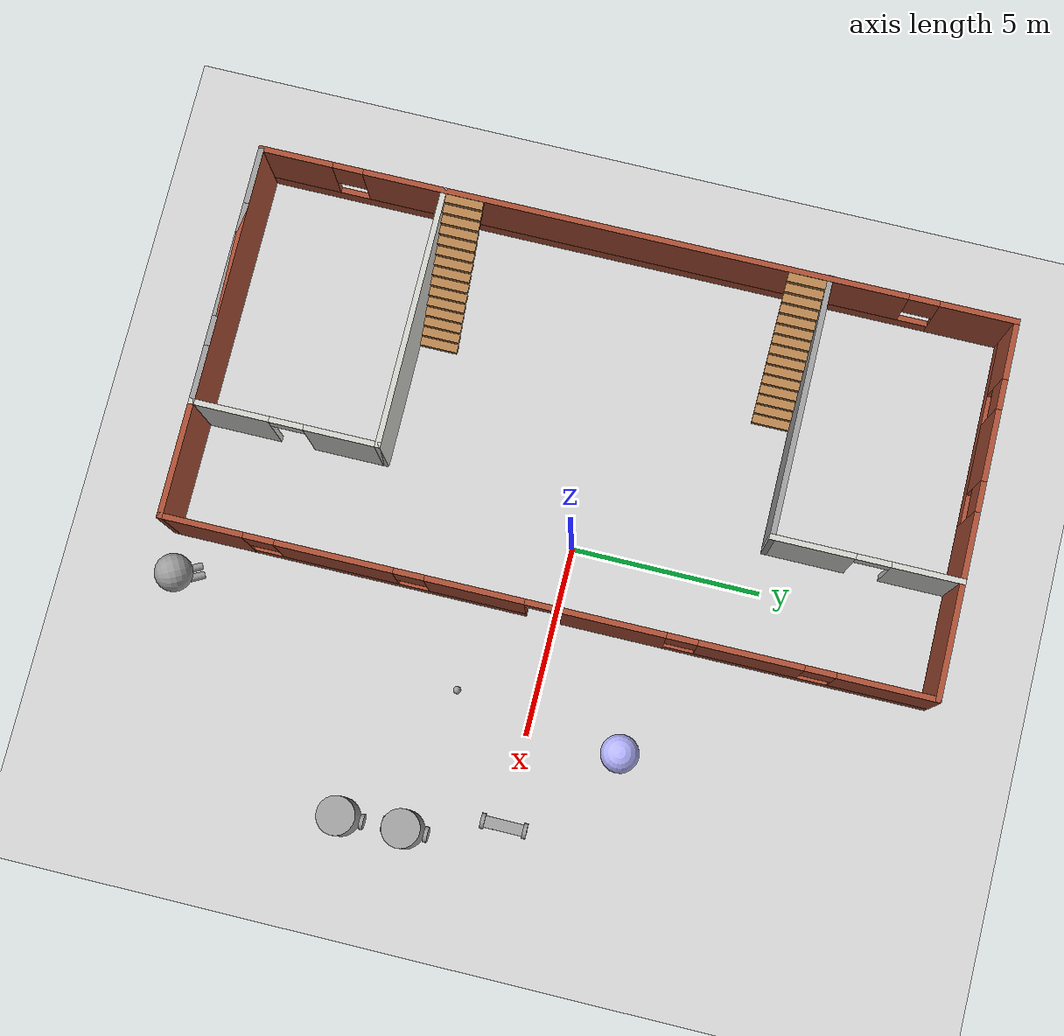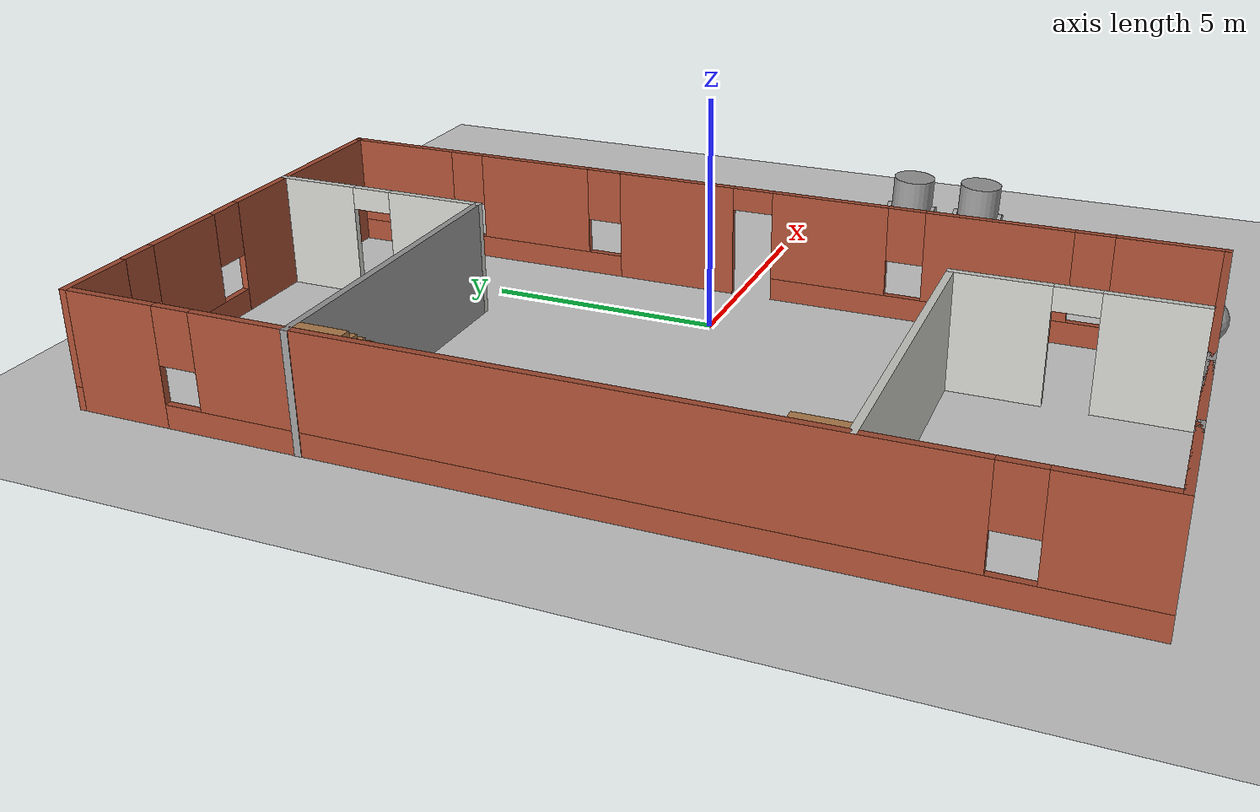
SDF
<sdf version="1.6">
 <world name="default">
  <plugin name="gazeboworld" filename="libgazeboworld.so"/>
  <light name="sun" type="directional">
   <pose>0 0 10 0 -0 0</pose>
   <diffuse>0.8 0.8 0.8 1</diffuse>
   <specular>0.2 0.2 0.2 1</specular>
   <attenuation>
    <range>1000</range>
    <constant>0.9</constant>
    <linear>0.01</linear>
    <quadratic>0.001</quadratic>
   </attenuation>
   <direction>-0.5 0.1 -0.9</direction>
  </light>
  <model name="ground_plane">
   <static>1</static>
   <link name="link">
    <collision name="collision">
     <geometry><plane><normal>0 0 1</normal><size>100 100</size></plane></geometry>
     <surface>
      <contact><collide_bitmask>65535</collide_bitmask></contact>
      <friction><ode><mu>100</mu><mu2>50</mu2></ode></friction>
     </surface>
    </collision>
    <visual name="visual">
     <cast_shadows>0</cast_shadows>
     <geometry><plane><normal>0 0 1</normal><size>100 100</size></plane></geometry>
     <material>
      <script><uri>file://media/materials/scripts/gazebo.material</uri><name>Gazebo/Grey</name></script>
     </material>
    </visual>
   </link>
  </model>
  <gravity>0 0 -9.8</gravity>
  <magnetic_field>6e-06 2.3e-05 -4.2e-05</magnetic_field>
  <atmosphere type="adiabatic"/>
  <physics name="default_physics" default="0" type="ode">
   <max_step_size>0.001</max_step_size>
   <real_time_factor>1</real_time_factor>
   <real_time_update_rate>1000</real_time_update_rate>
  </physics>
  <scene><ambient>0.4 0.4 0.4 1</ambient><background>0.7 0.7 0.7 1</background><shadows>1</shadows></scene>
  <spherical_coordinates>
   <surface_model>EARTH_WGS84</surface_model>
   <latitude_deg>0</latitude_deg>
   <longitude_deg>0</longitude_deg>
   <elevation>0</elevation>
   <heading_deg>0</heading_deg>
  </spherical_coordinates>
  <model name="twowheelsrobotModel">
   <link name="link_0">
    <pose>0 0 0.2 0 -0 0</pose>
    <inertial>
     <mass>1</mass>
     <inertia>
      <ixx>0.166667</ixx>
      <ixy>0</ixy>
      <ixz>0</ixz>
      <iyy>0.166667</iyy>
      <iyz>0</iyz>
      <izz>0.166667</izz>
     </inertia>
    </inertial>
    <visual name="visual">
     <geometry><box><size>0.3 1 0.1</size></box></geometry>
     <material>
      <lighting>1</lighting>
      <script><uri>file://media/materials/scripts/gazebo.material</uri><name>Gazebo/Grey</name></script>
      <shader type="pixel"><normal_map>__default__</normal_map></shader>
      <ambient>0.3 0.3 0.3 1</ambient>
      <diffuse>0.7 0.7 0.7 1</diffuse>
      <specular>0.01 0.01 0.01 1</specular>
      <emissive>0 0 0 1</emissive>
     </material>
    </visual>
    <collision name="collision">
     <geometry><box><size>0.3 1 0.1</size></box></geometry>
     <surface>
      <friction>
       <ode><mu>1</mu><mu2>1</mu2><fdir1>0 0 0</fdir1><slip1>0</slip1><slip2>0</slip2></ode>
       <torsional>
        <coefficient>1</coefficient>
        <patch_radius>0</patch_radius>
        <surface_radius>0</surface_radius>
        <use_patch_radius>1</use_patch_radius>
        <ode><slip>0</slip></ode>
       </torsional>
      </friction>
      <bounce><restitution_coefficient>0</restitution_coefficient><threshold>1e+06</threshold></bounce>
      <contact>
       <collide_without_contact>0</collide_without_contact>
       <collide_without_contact_bitmask>1</collide_without_contact_bitmask>
       <collide_bitmask>1</collide_bitmask>
       <ode>
        <soft_cfm>0</soft_cfm>
        <soft_erp>0.2</soft_erp>
        <kp>1e+13</kp>
        <kd>1</kd>
        <max_vel>0.01</max_vel>
        <min_depth>0</min_depth>
       </ode>
       <bullet>
        <split_impulse>1</split_impulse>
        <split_impulse_penetration_threshold>-0.01</split_impulse_penetration_threshold>
        <soft_cfm>0</soft_cfm>
        <soft_erp>0.2</soft_erp>
        <kp>1e+13</kp>
        <kd>1</kd>
       </bullet>
      </contact>
     </surface>
    </collision>
   </link>
   <link name="link_1">
    <pose>0 -0.550019 0.2 1.5707 -0 0</pose>
    <inertial>
     <mass>1</mass>
     <inertia><ixx>0.145833</ixx><ixy>0</ixy><ixz>0</ixz><iyy>0.145833</iyy><iyz>0</iyz><izz>0.125</izz></inertia>
    </inertial>
    <visual name="visual">
     <geometry><cylinder><radius>0.2</radius><length>0.1</length></cylinder></geometry>
     <material>
      <lighting>1</lighting>
      <script><uri>file://media/materials/scripts/gazebo.material</uri><name>Gazebo/Grey</name></script>
      <shader type="pixel"><normal_map>__default__</normal_map></shader>
      <ambient>0.3 0.3 0.3 1</ambient>
      <diffuse>0.7 0.7 0.7 1</diffuse>
      <specular>0.01 0.01 0.01 1</specular>
      <emissive>0 0 0 1</emissive>
     </material>
    </visual>
    <collision name="collision">
     <geometry><cylinder><radius>0.2</radius><length>0.1</length></cylinder></geometry>
     <surface>
      <friction>
       <ode><mu>1</mu><mu2>1</mu2><fdir1>0 0 0</fdir1><slip1>0</slip1><slip2>0</slip2></ode>
       <torsional>
        <coefficient>1</coefficient>
        <patch_radius>0</patch_radius>
        <surface_radius>0</surface_radius>
        <use_patch_radius>1</use_patch_radius>
        <ode><slip>0</slip></ode>
       </torsional>
      </friction>
      <bounce><restitution_coefficient>0</restitution_coefficient><threshold>1e+06</threshold></bounce>
      <contact>
       <collide_without_contact>0</collide_without_contact>
       <collide_without_contact_bitmask>1</collide_without_contact_bitmask>
       <collide_bitmask>1</collide_bitmask>
       <ode>
        <soft_cfm>0</soft_cfm>
        <soft_erp>0.2</soft_erp>
        <kp>1e+13</kp>
        <kd>1</kd>
        <max_vel>0.01</max_vel>
        <min_depth>0</min_depth>
       </ode>
       <bullet>
        <split_impulse>1</split_impulse>
        <split_impulse_penetration_threshold>-0.01</split_impulse_penetration_threshold>
        <soft_cfm>0</soft_cfm>
        <soft_erp>0.2</soft_erp>
        <kp>1e+13</kp>
        <kd>1</kd>
       </bullet>
      </contact>
     </surface>
    </collision>
   </link>
   <link name="link_1_clone">
    <pose>0 0.550019 0.2 1.5707 -0 0</pose>
    <inertial>
     <mass>1</mass>
     <inertia><ixx>0.145833</ixx><ixy>0</ixy><ixz>0</ixz><iyy>0.145833</iyy><iyz>0</iyz><izz>0.125</izz></inertia>
    </inertial>
    <visual name="visual">
     <geometry><cylinder><radius>0.2</radius><length>0.1</length></cylinder></geometry>
     <material>
      <lighting>1</lighting>
      <script><uri>file://media/materials/scripts/gazebo.material</uri><name>Gazebo/Grey</name></script>
      <shader type="pixel"><normal_map>__default__</normal_map></shader>
      <ambient>0.3 0.3 0.3 1</ambient>
      <diffuse>0.7 0.7 0.7 1</diffuse>
      <specular>0.01 0.01 0.01 1</specular>
      <emissive>0 0 0 1</emissive>
     </material>
    </visual>
    <collision name="collision">
     <geometry><cylinder><radius>0.2</radius><length>0.1</length></cylinder></geometry>
     <surface>
      <friction>
       <ode><mu>1</mu><mu2>1</mu2><fdir1>0 0 0</fdir1><slip1>0</slip1><slip2>0</slip2></ode>
       <torsional>
        <coefficient>1</coefficient>
        <patch_radius>0</patch_radius>
        <surface_radius>0</surface_radius>
        <use_patch_radius>1</use_patch_radius>
        <ode><slip>0</slip></ode>
       </torsional>
      </friction>
      <bounce><restitution_coefficient>0</restitution_coefficient><threshold>1e+06</threshold></bounce>
      <contact>
       <collide_without_contact>0</collide_without_contact>
       <collide_without_contact_bitmask>1</collide_without_contact_bitmask>
       <collide_bitmask>1</collide_bitmask>
       <ode>
        <soft_cfm>0</soft_cfm>
        <soft_erp>0.2</soft_erp>
        <kp>1e+13</kp>
        <kd>1</kd>
        <max_vel>0.01</max_vel>
        <min_depth>0</min_depth>
       </ode>
       <bullet>
        <split_impulse>1</split_impulse>
        <split_impulse_penetration_threshold>-0.01</split_impulse_penetration_threshold>
        <soft_cfm>0</soft_cfm>
        <soft_erp>0.2</soft_erp>
        <kp>1e+13</kp>
        <kd>1</kd>
       </bullet>
      </contact>
     </surface>
    </collision>
   </link>
   <joint name="link_0_JOINT_0" type="revolute">
    <parent>link_0</parent>
    <child>link_1</child>
    <axis>
     <xyz>0 0 1</xyz>
     <use_parent_model_frame>0</use_parent_model_frame>
     <limit>
      <lower>-1.79769e+308</lower>
      <upper>1.79769e+308</upper>
      <effort>-1</effort>
      <velocity>-1</velocity>
     </limit>
     <dynamics>
      <spring_reference>0</spring_reference>
      <spring_stiffness>0</spring_stiffness>
      <damping>0</damping>
     </dynamics>
    </axis>
    <physics>
     <ode><limit><cfm>0</cfm><erp>0.2</erp></limit><suspension><cfm>0</cfm><erp>0.2</erp></suspension></ode>
    </physics>
   </joint>
   <joint name="link_0_JOINT_1" type="revolute">
    <parent>link_0</parent>
    <child>link_1_clone</child>
    <axis>
     <xyz>0 0 1</xyz>
     <use_parent_model_frame>0</use_parent_model_frame>
     <limit>
      <lower>-1.79769e+308</lower>
      <upper>1.79769e+308</upper>
      <effort>-1</effort>
      <velocity>-1</velocity>
     </limit>
     <dynamics>
      <spring_reference>0</spring_reference>
      <spring_stiffness>0</spring_stiffness>
      <damping>0</damping>
     </dynamics>
    </axis>
    <physics>
     <ode><limit><cfm>0</cfm><erp>0.2</erp></limit><suspension><cfm>0</cfm><erp>0.2</erp></suspension></ode>
    </physics>
   </joint>
   <static>0</static>
   <pose>7.34774 0 5e-06 0 -0 0</pose>
  </model>
  <model name="building01">
   <pose>-3.01648 -0.202483 0 0 -0 1.57461</pose>
   <link name="Stairs_0">
    <visual name="Stairs_0_Visual_0">
     <pose>-4.49569 1.4753 0.083 0 -0 -3.14159</pose>
     <geometry><box><size>1 0.233333 0.166</size></box></geometry>
     <material>
      <script><uri>file://media/materials/scripts/gazebo.material</uri><name>Gazebo/Wood</name></script>
      <ambient>0.760784 0.662745 0.627451 1</ambient>
     </material>
     <meta><layer>0</layer></meta>
    </visual>
    <collision name="Stairs_0_Collision_0">
     <geometry><box><size>1 0.233333 0.166</size></box></geometry>
     <pose>-4.49569 1.4753 0.083 0 -0 -3.14159</pose>
    </collision>
    <visual name="Stairs_0_Visual_1">
     <pose>-4.49569 1.70863 0.249 0 -0 -3.14159</pose>
     <geometry><box><size>1 0.233333 0.166</size></box></geometry>
     <material>
      <script><uri>file://media/materials/scripts/gazebo.material</uri><name>Gazebo/Wood</name></script>
      <ambient>0.760784 0.662745 0.627451 1</ambient>
     </material>
     <meta><layer>0</layer></meta>
    </visual>
    <collision name="Stairs_0_Collision_1">
     <geometry><box><size>1 0.233333 0.166</size></box></geometry>
     <pose>-4.49569 1.70863 0.249 0 -0 -3.14159</pose>
    </collision>
    <visual name="Stairs_0_Visual_2">
     <pose>-4.49569 1.94196 0.415 0 -0 -3.14159</pose>
     <geometry><box><size>1 0.233333 0.166</size></box></geometry>
     <material>
      <script><uri>file://media/materials/scripts/gazebo.material</uri><name>Gazebo/Wood</name></script>
      <ambient>0.760784 0.662745 0.627451 1</ambient>
     </material>
     <meta><layer>0</layer></meta>
    </visual>
    <collision name="Stairs_0_Collision_2">
     <geometry><box><size>1 0.233333 0.166</size></box></geometry>
     <pose>-4.49569 1.94196 0.415 0 -0 -3.14159</pose>
    </collision>
    <visual name="Stairs_0_Visual_3">
     <pose>-4.49569 2.1753 0.581 0 -0 -3.14159</pose>
     <geometry><box><size>1 0.233333 0.166</size></box></geometry>
     <material>
      <script><uri>file://media/materials/scripts/gazebo.material</uri><name>Gazebo/Wood</name></script>
      <ambient>0.760784 0.662745 0.627451 1</ambient>
     </material>
     <meta><layer>0</layer></meta>
    </visual>
    <collision name="Stairs_0_Collision_3">
     <geometry><box><size>1 0.233333 0.166</size></box></geometry>
     <pose>-4.49569 2.1753 0.581 0 -0 -3.14159</pose>
    </collision>
    <visual name="Stairs_0_Visual_4">
     <pose>-4.49569 2.40863 0.747 0 -0 -3.14159</pose>
     <geometry><box><size>1 0.233333 0.166</size></box></geometry>
     <material>
      <script><uri>file://media/materials/scripts/gazebo.material</uri><name>Gazebo/Wood</name></script>
      <ambient>0.760784 0.662745 0.627451 1</ambient>
     </material>
     <meta><layer>0</layer></meta>
    </visual>
    <collision name="Stairs_0_Collision_4">
     <geometry><box><size>1 0.233333 0.166</size></box></geometry>
     <pose>-4.49569 2.40863 0.747 0 -0 -3.14159</pose>
    </collision>
    <visual name="Stairs_0_Visual_5">
     <pose>-4.49569 2.64196 0.913 0 -0 -3.14159</pose>
     <geometry><box><size>1 0.233333 0.166</size></box></geometry>
     <material>
      <script><uri>file://media/materials/scripts/gazebo.material</uri><name>Gazebo/Wood</name></script>
      <ambient>0.760784 0.662745 0.627451 1</ambient>
     </material>
     <meta><layer>0</layer></meta>
    </visual>
    <collision name="Stairs_0_Collision_5">
     <geometry><box><size>1 0.233333 0.166</size></box></geometry>
     <pose>-4.49569 2.64196 0.913 0 -0 -3.14159</pose>
    </collision>
    <visual name="Stairs_0_Visual_6">
     <pose>-4.49569 2.87529 1.079 0 -0 -3.14159</pose>
     <geometry><box><size>1 0.233333 0.166</size></box></geometry>
     <material>
      <script><uri>file://media/materials/scripts/gazebo.material</uri><name>Gazebo/Wood</name></script>
      <ambient>0.760784 0.662745 0.627451 1</ambient>
     </material>
     <meta><layer>0</layer></meta>
    </visual>
    <collision name="Stairs_0_Collision_6">
     <geometry><box><size>1 0.233333 0.166</size></box></geometry>
     <pose>-4.49569 2.87529 1.079 0 -0 -3.14159</pose>
    </collision>
    <visual name="Stairs_0_Visual_7">
     <pose>-4.49569 3.10863 1.245 0 -0 -3.14159</pose>
     <geometry><box><size>1 0.233333 0.166</size></box></geometry>
     <material>
      <script><uri>file://media/materials/scripts/gazebo.material</uri><name>Gazebo/Wood</name></script>
      <ambient>0.760784 0.662745 0.627451 1</ambient>
     </material>
     <meta><layer>0</layer></meta>
    </visual>
    <collision name="Stairs_0_Collision_7">
     <geometry><box><size>1 0.233333 0.166</size></box></geometry>
     <pose>-4.49569 3.10863 1.245 0 -0 -3.14159</pose>
    </collision>
    <visual name="Stairs_0_Visual_8">
     <pose>-4.49569 3.34196 1.411 0 -0 -3.14159</pose>
     <geometry><box><size>1 0.233333 0.166</size></box></geometry>
     <material>
      <script><uri>file://media/materials/scripts/gazebo.material</uri><name>Gazebo/Wood</name></script>
      <ambient>0.760784 0.662745 0.627451 1</ambient>
     </material>
     <meta><layer>0</layer></meta>
    </visual>
    <collision name="Stairs_0_Collision_8">
     <geometry><box><size>1 0.233333 0.166</size></box></geometry>
     <pose>-4.49569 3.34196 1.411 0 -0 -3.14159</pose>
    </collision>
    <visual name="Stairs_0_Visual_9">
     <pose>-4.49569 3.5753 1.577 0 -0 -3.14159</pose>
     <geometry><box><size>1 0.233333 0.166</size></box></geometry>
     <material>
      <script><uri>file://media/materials/scripts/gazebo.material</uri><name>Gazebo/Wood</name></script>
      <ambient>0.760784 0.662745 0.627451 1</ambient>
     </material>
     <meta><layer>0</layer></meta>
    </visual>
    <collision name="Stairs_0_Collision_9">
     <geometry><box><size>1 0.233333 0.166</size></box></geometry>
     <pose>-4.49569 3.5753 1.577 0 -0 -3.14159</pose>
    </collision>
    <visual name="Stairs_0_Visual_10">
     <pose>-4.49569 3.80863 1.743 0 -0 -3.14159</pose>
     <geometry><box><size>1 0.233333 0.166</size></box></geometry>
     <material>
      <script><uri>file://media/materials/scripts/gazebo.material</uri><name>Gazebo/Wood</name></script>
      <ambient>0.760784 0.662745 0.627451 1</ambient>
     </material>
     <meta><layer>0</layer></meta>
    </visual>
    <collision name="Stairs_0_Collision_10">
     <geometry><box><size>1 0.233333 0.166</size></box></geometry>
     <pose>-4.49569 3.80863 1.743 0 -0 -3.14159</pose>
    </collision>
    <visual name="Stairs_0_Visual_11">
     <pose>-4.49569 4.04196 1.909 0 -0 -3.14159</pose>
     <geometry><box><size>1 0.233333 0.166</size></box></geometry>
     <material>
      <script><uri>file://media/materials/scripts/gazebo.material</uri><name>Gazebo/Wood</name></script>
      <ambient>0.760784 0.662745 0.627451 1</ambient>
     </material>
     <meta><layer>0</layer></meta>
    </visual>
    <collision name="Stairs_0_Collision_11">
     <geometry><box><size>1 0.233333 0.166</size></box></geometry>
     <pose>-4.49569 4.04196 1.909 0 -0 -3.14159</pose>
    </collision>
    <visual name="Stairs_0_Visual_12">
     <pose>-4.49569 4.27529 2.075 0 -0 -3.14159</pose>
     <geometry><box><size>1 0.233333 0.166</size></box></geometry>
     <material>
      <script><uri>file://media/materials/scripts/gazebo.material</uri><name>Gazebo/Wood</name></script>
      <ambient>0.760784 0.662745 0.627451 1</ambient>
     </material>
     <meta><layer>0</layer></meta>
    </visual>
    <collision name="Stairs_0_Collision_12">
     <geometry><box><size>1 0.233333 0.166</size></box></geometry>
     <pose>-4.49569 4.27529 2.075 0 -0 -3.14159</pose>
    </collision>
    <visual name="Stairs_0_Visual_13">
     <pose>-4.49569 4.50863 2.241 0 -0 -3.14159</pose>
     <geometry><box><size>1 0.233333 0.166</size></box></geometry>
     <material>
      <script><uri>file://media/materials/scripts/gazebo.material</uri><name>Gazebo/Wood</name></script>
      <ambient>0.760784 0.662745 0.627451 1</ambient>
     </material>
     <meta><layer>0</layer></meta>
    </visual>
    <collision name="Stairs_0_Collision_13">
     <geometry><box><size>1 0.233333 0.166</size></box></geometry>
     <pose>-4.49569 4.50863 2.241 0 -0 -3.14159</pose>
    </collision>
    <visual name="Stairs_0_Visual_14">
     <pose>-4.49569 4.74196 2.407 0 -0 -3.14159</pose>
     <geometry><box><size>1 0.233333 0.166</size></box></geometry>
     <material>
      <script><uri>file://media/materials/scripts/gazebo.material</uri><name>Gazebo/Wood</name></script>
      <ambient>0.760784 0.662745 0.627451 1</ambient>
     </material>
     <meta><layer>0</layer></meta>
    </visual>
    <collision name="Stairs_0_Collision_14">
     <geometry><box><size>1 0.233333 0.166</size></box></geometry>
     <pose>-4.49569 4.74196 2.407 0 -0 -3.14159</pose>
    </collision>
   </link>
   <link name="Stairs_1">
    <visual name="Stairs_1_Visual_0">
     <pose>4.50728 1.45825 0.083333 0 -0 -3.14159</pose>
     <geometry><box><size>1 0.233333 0.166667</size></box></geometry>
     <material>
      <script><uri>file://media/materials/scripts/gazebo.material</uri><name>Gazebo/Wood</name></script>
      <ambient>1 1 1 1</ambient>
     </material>
     <meta><layer>0</layer></meta>
    </visual>
    <collision name="Stairs_1_Collision_0">
     <geometry><box><size>1 0.233333 0.166667</size></box></geometry>
     <pose>4.50728 1.45825 0.083333 0 -0 -3.14159</pose>
    </collision>
    <visual name="Stairs_1_Visual_1">
     <pose>4.50728 1.69158 0.25 0 -0 -3.14159</pose>
     <geometry><box><size>1 0.233333 0.166667</size></box></geometry>
     <material>
      <script><uri>file://media/materials/scripts/gazebo.material</uri><name>Gazebo/Wood</name></script>
      <ambient>1 1 1 1</ambient>
     </material>
     <meta><layer>0</layer></meta>
    </visual>
    <collision name="Stairs_1_Collision_1">
     <geometry><box><size>1 0.233333 0.166667</size></box></geometry>
     <pose>4.50728 1.69158 0.25 0 -0 -3.14159</pose>
    </collision>
    <visual name="Stairs_1_Visual_2">
     <pose>4.50728 1.92491 0.416667 0 -0 -3.14159</pose>
     <geometry><box><size>1 0.233333 0.166667</size></box></geometry>
     <material>
      <script><uri>file://media/materials/scripts/gazebo.material</uri><name>Gazebo/Wood</name></script>
      <ambient>1 1 1 1</ambient>
     </material>
     <meta><layer>0</layer></meta>
    </visual>
    <collision name="Stairs_1_Collision_2">
     <geometry><box><size>1 0.233333 0.166667</size></box></geometry>
     <pose>4.50728 1.92491 0.416667 0 -0 -3.14159</pose>
    </collision>
    <visual name="Stairs_1_Visual_3">
     <pose>4.50728 2.15825 0.583333 0 -0 -3.14159</pose>
     <geometry><box><size>1 0.233333 0.166667</size></box></geometry>
     <material>
      <script><uri>file://media/materials/scripts/gazebo.material</uri><name>Gazebo/Wood</name></script>
      <ambient>1 1 1 1</ambient>
     </material>
     <meta><layer>0</layer></meta>
    </visual>
    <collision name="Stairs_1_Collision_3">
     <geometry><box><size>1 0.233333 0.166667</size></box></geometry>
     <pose>4.50728 2.15825 0.583333 0 -0 -3.14159</pose>
    </collision>
    <visual name="Stairs_1_Visual_4">
     <pose>4.50728 2.39158 0.75 0 -0 -3.14159</pose>
     <geometry><box><size>1 0.233333 0.166667</size></box></geometry>
     <material>
      <script><uri>file://media/materials/scripts/gazebo.material</uri><name>Gazebo/Wood</name></script>
      <ambient>1 1 1 1</ambient>
     </material>
     <meta><layer>0</layer></meta>
    </visual>
    <collision name="Stairs_1_Collision_4">
     <geometry><box><size>1 0.233333 0.166667</size></box></geometry>
     <pose>4.50728 2.39158 0.75 0 -0 -3.14159</pose>
    </collision>
    <visual name="Stairs_1_Visual_5">
     <pose>4.50728 2.62491 0.916667 0 -0 -3.14159</pose>
     <geometry><box><size>1 0.233333 0.166667</size></box></geometry>
     <material>
      <script><uri>file://media/materials/scripts/gazebo.material</uri><name>Gazebo/Wood</name></script>
      <ambient>1 1 1 1</ambient>
     </material>
     <meta><layer>0</layer></meta>
    </visual>
    <collision name="Stairs_1_Collision_5">
     <geometry><box><size>1 0.233333 0.166667</size></box></geometry>
     <pose>4.50728 2.62491 0.916667 0 -0 -3.14159</pose>
    </collision>
    <visual name="Stairs_1_Visual_6">
     <pose>4.50728 2.85825 1.08333 0 -0 -3.14159</pose>
     <geometry><box><size>1 0.233333 0.166667</size></box></geometry>
     <material>
      <script><uri>file://media/materials/scripts/gazebo.material</uri><name>Gazebo/Wood</name></script>
      <ambient>1 1 1 1</ambient>
     </material>
     <meta><layer>0</layer></meta>
    </visual>
    <collision name="Stairs_1_Collision_6">
     <geometry><box><size>1 0.233333 0.166667</size></box></geometry>
     <pose>4.50728 2.85825 1.08333 0 -0 -3.14159</pose>
    </collision>
    <visual name="Stairs_1_Visual_7">
     <pose>4.50728 3.09158 1.25 0 -0 -3.14159</pose>
     <geometry><box><size>1 0.233333 0.166667</size></box></geometry>
     <material>
      <script><uri>file://media/materials/scripts/gazebo.material</uri><name>Gazebo/Wood</name></script>
      <ambient>1 1 1 1</ambient>
     </material>
     <meta><layer>0</layer></meta>
    </visual>
    <collision name="Stairs_1_Collision_7">
     <geometry><box><size>1 0.233333 0.166667</size></box></geometry>
     <pose>4.50728 3.09158 1.25 0 -0 -3.14159</pose>
    </collision>
    <visual name="Stairs_1_Visual_8">
     <pose>4.50728 3.32491 1.41667 0 -0 -3.14159</pose>
     <geometry><box><size>1 0.233333 0.166667</size></box></geometry>
     <material>
      <script><uri>file://media/materials/scripts/gazebo.material</uri><name>Gazebo/Wood</name></script>
      <ambient>1 1 1 1</ambient>
     </material>
     <meta><layer>0</layer></meta>
    </visual>
    <collision name="Stairs_1_Collision_8">
     <geometry><box><size>1 0.233333 0.166667</size></box></geometry>
     <pose>4.50728 3.32491 1.41667 0 -0 -3.14159</pose>
    </collision>
    <visual name="Stairs_1_Visual_9">
     <pose>4.50728 3.55825 1.58333 0 -0 -3.14159</pose>
     <geometry><box><size>1 0.233333 0.166667</size></box></geometry>
     <material>
      <script><uri>file://media/materials/scripts/gazebo.material</uri><name>Gazebo/Wood</name></script>
      <ambient>1 1 1 1</ambient>
     </material>
     <meta><layer>0</layer></meta>
    </visual>
    <collision name="Stairs_1_Collision_9">
     <geometry><box><size>1 0.233333 0.166667</size></box></geometry>
     <pose>4.50728 3.55825 1.58333 0 -0 -3.14159</pose>
    </collision>
    <visual name="Stairs_1_Visual_10">
     <pose>4.50728 3.79158 1.75 0 -0 -3.14159</pose>
     <geometry><box><size>1 0.233333 0.166667</size></box></geometry>
     <material>
      <script><uri>file://media/materials/scripts/gazebo.material</uri><name>Gazebo/Wood</name></script>
      <ambient>1 1 1 1</ambient>
     </material>
     <meta><layer>0</layer></meta>
    </visual>
    <collision name="Stairs_1_Collision_10">
     <geometry><box><size>1 0.233333 0.166667</size></box></geometry>
     <pose>4.50728 3.79158 1.75 0 -0 -3.14159</pose>
    </collision>
    <visual name="Stairs_1_Visual_11">
     <pose>4.50728 4.02491 1.91667 0 -0 -3.14159</pose>
     <geometry><box><size>1 0.233333 0.166667</size></box></geometry>
     <material>
      <script><uri>file://media/materials/scripts/gazebo.material</uri><name>Gazebo/Wood</name></script>
      <ambient>1 1 1 1</ambient>
     </material>
     <meta><layer>0</layer></meta>
    </visual>
    <collision name="Stairs_1_Collision_11">
     <geometry><box><size>1 0.233333 0.166667</size></box></geometry>
     <pose>4.50728 4.02491 1.91667 0 -0 -3.14159</pose>
    </collision>
    <visual name="Stairs_1_Visual_12">
     <pose>4.50728 4.25825 2.08333 0 -0 -3.14159</pose>
     <geometry><box><size>1 0.233333 0.166667</size></box></geometry>
     <material>
      <script><uri>file://media/materials/scripts/gazebo.material</uri><name>Gazebo/Wood</name></script>
      <ambient>1 1 1 1</ambient>
     </material>
     <meta><layer>0</layer></meta>
    </visual>
    <collision name="Stairs_1_Collision_12">
     <geometry><box><size>1 0.233333 0.166667</size></box></geometry>
     <pose>4.50728 4.25825 2.08333 0 -0 -3.14159</pose>
    </collision>
    <visual name="Stairs_1_Visual_13">
     <pose>4.50728 4.49158 2.25 0 -0 -3.14159</pose>
     <geometry><box><size>1 0.233333 0.166667</size></box></geometry>
     <material>
      <script><uri>file://media/materials/scripts/gazebo.material</uri><name>Gazebo/Wood</name></script>
      <ambient>1 1 1 1</ambient>
     </material>
     <meta><layer>0</layer></meta>
    </visual>
    <collision name="Stairs_1_Collision_13">
     <geometry><box><size>1 0.233333 0.166667</size></box></geometry>
     <pose>4.50728 4.49158 2.25 0 -0 -3.14159</pose>
    </collision>
    <visual name="Stairs_1_Visual_14">
     <pose>4.50728 4.72491 2.41667 0 -0 -3.14159</pose>
     <geometry><box><size>1 0.233333 0.166667</size></box></geometry>
     <material>
      <script><uri>file://media/materials/scripts/gazebo.material</uri><name>Gazebo/Wood</name></script>
      <ambient>1 1 1 1</ambient>
     </material>
     <meta><layer>0</layer></meta>
    </visual>
    <collision name="Stairs_1_Collision_14">
     <geometry><box><size>1 0.233333 0.166667</size></box></geometry>
     <pose>4.50728 4.72491 2.41667 0 -0 -3.14159</pose>
    </collision>
   </link>
   <link name="Wall_16">
    <pose>7.50105 -1.91931 0 0 -0 3.14159</pose>
    <visual name="Wall_16_Visual_0">
     <pose>-1.55703 0 1.25 0 -0 0</pose>
     <geometry><box><size>1.88594 0.15 2.5</size></box></geometry>
     <material>
      <script><uri>file://media/materials/scripts/gazebo.material</uri><name>Gazebo/CeilingTiled</name></script>
      <ambient>1 1 1 1</ambient>
     </material>
     <meta><layer>0</layer></meta>
    </visual>
    <collision name="Wall_16_Collision_0">
     <geometry><box><size>1.88594 0.15 2.5</size></box></geometry>
     <pose>-1.55703 0 1.25 0 -0 0</pose>
    </collision>
    <visual name="Wall_16_Visual_1">
     <pose>1.39297 0 1.25 0 -0 0</pose>
     <geometry><box><size>2.21406 0.15 2.5</size></box></geometry>
     <material>
      <script><uri>file://media/materials/scripts/gazebo.material</uri><name>Gazebo/CeilingTiled</name></script>
      <ambient>1 1 1 1</ambient>
     </material>
     <meta><layer>0</layer></meta>
    </visual>
    <collision name="Wall_16_Collision_1">
     <geometry><box><size>2.21406 0.15 2.5</size></box></geometry>
     <pose>1.39297 0 1.25 0 -0 0</pose>
    </collision>
    <visual name="Wall_16_Visual_2">
     <pose>-0.164063 0 2.25 0 -0 0</pose>
     <geometry><box><size>0.9 0.15 0.5</size></box></geometry>
     <material>
      <script><uri>file://media/materials/scripts/gazebo.material</uri><name>Gazebo/CeilingTiled</name></script>
      <ambient>1 1 1 1</ambient>
     </material>
     <meta><layer>0</layer></meta>
    </visual>
    <collision name="Wall_16_Collision_2">
     <geometry><box><size>0.9 0.15 0.5</size></box></geometry>
     <pose>-0.164063 0 2.25 0 -0 0</pose>
    </collision>
   </link>
   <link name="Wall_17">
    <collision name="Wall_17_Collision">
     <geometry><box><size>7 0.15 2.5</size></box></geometry>
     <pose>0 0 1.25 0 -0 0</pose>
    </collision>
    <visual name="Wall_17_Visual">
     <pose>0 0 1.25 0 -0 0</pose>
     <geometry><box><size>7 0.15 2.5</size></box></geometry>
     <material>
      <script><uri>file://media/materials/scripts/gazebo.material</uri><name>Gazebo/Grey</name></script>
      <ambient>1 1 1 1</ambient>
     </material>
     <meta><layer>0</layer></meta>
    </visual>
    <pose>5.07605 1.50569 0 0 -0 1.5708</pose>
   </link>
   <link name="Wall_3">
    <collision name="Wall_3_Collision">
     <geometry><box><size>10 0.15 2.5</size></box></geometry>
     <pose>0 0 1.25 0 -0 0</pose>
    </collision>
    <visual name="Wall_3_Visual">
     <pose>0 0 1.25 0 -0 0</pose>
     <geometry><box><size>10 0.15 2.5</size></box></geometry>
     <material>
      <script><uri>file://media/materials/scripts/gazebo.material</uri><name>Gazebo/Bricks</name></script>
      <ambient>1 1 1 1</ambient>
     </material>
     <meta><layer>0</layer></meta>
    </visual>
    <pose>-9.92605 -0.005693 0 0 0 -1.5708</pose>
   </link>
   <link name="Wall_4">
    <pose>-0.001048 -4.93069 0 0 -0 0</pose>
    <visual name="Wall_4_Visual_0">
     <pose>-8.8894 0 1.25 0 -0 0</pose>
     <geometry><box><size>2.22121 0.15 2.5</size></box></geometry>
     <material>
      <script><uri>file://media/materials/scripts/gazebo.material</uri><name>Gazebo/Bricks</name></script>
      <ambient>1 1 1 1</ambient>
     </material>
     <meta><layer>0</layer></meta>
    </visual>
    <collision name="Wall_4_Collision_0">
     <geometry><box><size>2.22121 0.15 2.5</size></box></geometry>
     <pose>-8.8894 0 1.25 0 -0 0</pose>
    </collision>
    <visual name="Wall_4_Visual_1">
     <pose>1.70737 0 1.25 0 -0 0</pose>
     <geometry><box><size>2.7101 0.15 2.5</size></box></geometry>
     <material>
      <script><uri>file://media/materials/scripts/gazebo.material</uri><name>Gazebo/Bricks</name></script>
      <ambient>1 1 1 1</ambient>
     </material>
     <meta><layer>0</layer></meta>
    </visual>
    <collision name="Wall_4_Collision_1">
     <geometry><box><size>2.7101 0.15 2.5</size></box></geometry>
     <pose>1.70737 0 1.25 0 -0 0</pose>
    </collision>
    <visual name="Wall_4_Visual_2">
     <pose>-4.16324 0 0.25 0 -0 0</pose>
     <geometry><box><size>7.23111 0.15 0.5</size></box></geometry>
     <material>
      <script><uri>file://media/materials/scripts/gazebo.material</uri><name>Gazebo/Bricks</name></script>
      <ambient>1 1 1 1</ambient>
     </material>
     <meta><layer>0</layer></meta>
    </visual>
    <collision name="Wall_4_Collision_2">
     <geometry><box><size>7.23111 0.15 0.5</size></box></geometry>
     <pose>-4.16324 0 0.25 0 -0 0</pose>
    </collision>
    <visual name="Wall_4_Visual_3">
     <pose>6.53121 0 0.25 0 -0 0</pose>
     <geometry><box><size>6.93758 0.15 0.5</size></box></geometry>
     <material>
      <script><uri>file://media/materials/scripts/gazebo.material</uri><name>Gazebo/Bricks</name></script>
      <ambient>1 1 1 1</ambient>
     </material>
     <meta><layer>0</layer></meta>
    </visual>
    <collision name="Wall_4_Collision_3">
     <geometry><box><size>6.93758 0.15 0.5</size></box></geometry>
     <pose>6.53121 0 0.25 0 -0 0</pose>
    </collision>
    <visual name="Wall_4_Visual_4">
     <pose>-5.44789 0 1.5 0 -0 0</pose>
     <geometry><box><size>3.06181 0.15 2</size></box></geometry>
     <material>
      <script><uri>file://media/materials/scripts/gazebo.material</uri><name>Gazebo/Bricks</name></script>
      <ambient>1 1 1 1</ambient>
     </material>
     <meta><layer>0</layer></meta>
    </visual>
    <collision name="Wall_4_Collision_4">
     <geometry><box><size>3.06181 0.15 2</size></box></geometry>
     <pose>-5.44789 0 1.5 0 -0 0</pose>
    </collision>
    <visual name="Wall_4_Visual_5">
     <pose>-1.83233 0 1.5 0 -0 0</pose>
     <geometry><box><size>2.56931 0.15 2</size></box></geometry>
     <material>
      <script><uri>file://media/materials/scripts/gazebo.material</uri><name>Gazebo/Bricks</name></script>
      <ambient>1 1 1 1</ambient>
     </material>
     <meta><layer>0</layer></meta>
    </visual>
    <collision name="Wall_4_Collision_5">
     <geometry><box><size>2.56931 0.15 2</size></box></geometry>
     <pose>-1.83233 0 1.5 0 -0 0</pose>
    </collision>
    <visual name="Wall_4_Visual_6">
     <pose>-1.83233 0 1.5 0 -0 0</pose>
     <geometry><box><size>2.56931 0.15 2</size></box></geometry>
     <material>
      <script><uri>file://media/materials/scripts/gazebo.material</uri><name>Gazebo/Bricks</name></script>
      <ambient>1 1 1 1</ambient>
     </material>
     <meta><layer>0</layer></meta>
    </visual>
    <collision name="Wall_4_Collision_6">
     <geometry><box><size>2.56931 0.15 2</size></box></geometry>
     <pose>-1.83233 0 1.5 0 -0 0</pose>
    </collision>
    <visual name="Wall_4_Visual_7">
     <pose>5.2123 0 1.5 0 -0 0</pose>
     <geometry><box><size>2.69976 0.15 2</size></box></geometry>
     <material>
      <script><uri>file://media/materials/scripts/gazebo.material</uri><name>Gazebo/Bricks</name></script>
      <ambient>1 1 1 1</ambient>
     </material>
     <meta><layer>0</layer></meta>
    </visual>
    <collision name="Wall_4_Collision_7">
     <geometry><box><size>2.69976 0.15 2</size></box></geometry>
     <pose>5.2123 0 1.5 0 -0 0</pose>
    </collision>
    <visual name="Wall_4_Visual_8">
     <pose>8.68109 0 1.5 0 -0 0</pose>
     <geometry><box><size>2.63782 0.15 2</size></box></geometry>
     <material>
      <script><uri>file://media/materials/scripts/gazebo.material</uri><name>Gazebo/Bricks</name></script>
      <ambient>1 1 1 1</ambient>
     </material>
     <meta><layer>0</layer></meta>
    </visual>
    <collision name="Wall_4_Collision_8">
     <geometry><box><size>2.63782 0.15 2</size></box></geometry>
     <pose>8.68109 0 1.5 0 -0 0</pose>
    </collision>
    <visual name="Wall_4_Visual_9">
     <pose>-7.37879 0 1.9 0 -0 0</pose>
     <geometry><box><size>0.8 0.15 1.2</size></box></geometry>
     <material>
      <script><uri>file://media/materials/scripts/gazebo.material</uri><name>Gazebo/Bricks</name></script>
      <ambient>1 1 1 1</ambient>
     </material>
     <meta><layer>0</layer></meta>
    </visual>
    <collision name="Wall_4_Collision_9">
     <geometry><box><size>0.8 0.15 1.2</size></box></geometry>
     <pose>-7.37879 0 1.9 0 -0 0</pose>
    </collision>
    <visual name="Wall_4_Visual_10">
     <pose>3.46242 0 1.9 0 -0 0</pose>
     <geometry><box><size>0.8 0.15 1.2</size></box></geometry>
     <material>
      <script><uri>file://media/materials/scripts/gazebo.material</uri><name>Gazebo/Bricks</name></script>
      <ambient>1 1 1 1</ambient>
     </material>
     <meta><layer>0</layer></meta>
    </visual>
    <collision name="Wall_4_Collision_10">
     <geometry><box><size>0.8 0.15 1.2</size></box></geometry>
     <pose>3.46242 0 1.9 0 -0 0</pose>
    </collision>
    <visual name="Wall_4_Visual_11">
     <pose>-3.51699 0 1.9 0 -0 0</pose>
     <geometry><box><size>0.8 0.15 1.2</size></box></geometry>
     <material>
      <script><uri>file://media/materials/scripts/gazebo.material</uri><name>Gazebo/Bricks</name></script>
      <ambient>1 1 1 1</ambient>
     </material>
     <meta><layer>0</layer></meta>
    </visual>
    <collision name="Wall_4_Collision_11">
     <geometry><box><size>0.8 0.15 1.2</size></box></geometry>
     <pose>-3.51699 0 1.9 0 -0 0</pose>
    </collision>
    <visual name="Wall_4_Visual_12">
     <pose>6.96218 0 1.9 0 -0 0</pose>
     <geometry><box><size>0.8 0.15 1.2</size></box></geometry>
     <material>
      <script><uri>file://media/materials/scripts/gazebo.material</uri><name>Gazebo/Bricks</name></script>
      <ambient>1 1 1 1</ambient>
     </material>
     <meta><layer>0</layer></meta>
    </visual>
    <collision name="Wall_4_Collision_12">
     <geometry><box><size>0.8 0.15 1.2</size></box></geometry>
     <pose>6.96218 0 1.9 0 -0 0</pose>
    </collision>
    <visual name="Wall_4_Visual_13">
     <pose>-0.09768 0 2.25 0 -0 0</pose>
     <geometry><box><size>0.9 0.15 0.5</size></box></geometry>
     <material>
      <script><uri>file://media/materials/scripts/gazebo.material</uri><name>Gazebo/Bricks</name></script>
      <ambient>1 1 1 1</ambient>
     </material>
     <meta><layer>0</layer></meta>
    </visual>
    <collision name="Wall_4_Collision_13">
     <geometry><box><size>0.9 0.15 0.5</size></box></geometry>
     <pose>-0.09768 0 2.25 0 -0 0</pose>
    </collision>
    <visual name="Wall_4_Visual_14">
     <pose>-0.09768 0 2.25 0 -0 0</pose>
     <geometry><box><size>0.9 0.15 0.5</size></box></geometry>
     <material>
      <script><uri>file://media/materials/scripts/gazebo.material</uri><name>Gazebo/Bricks</name></script>
      <ambient>1 1 1 1</ambient>
     </material>
     <meta><layer>0</layer></meta>
    </visual>
    <collision name="Wall_4_Collision_14">
     <geometry><box><size>0.9 0.15 0.5</size></box></geometry>
     <pose>-0.09768 0 2.25 0 -0 0</pose>
    </collision>
   </link>
   <link name="Wall_5">
    <pose>9.92395 -0.005693 0 0 -0 1.5708</pose>
    <visual name="Wall_5_Visual_0">
     <pose>-2.55931 0 1.25 0 -0 0</pose>
     <geometry><box><size>4.88137 0.15 2.5</size></box></geometry>
     <material>
      <script><uri>file://media/materials/scripts/gazebo.material</uri><name>Gazebo/Bricks</name></script>
      <ambient>1 1 1 1</ambient>
     </material>
     <meta><layer>0</layer></meta>
    </visual>
    <collision name="Wall_5_Collision_0">
     <geometry><box><size>4.88137 0.15 2.5</size></box></geometry>
     <pose>-2.55931 0 1.25 0 -0 0</pose>
    </collision>
    <visual name="Wall_5_Visual_1">
     <pose>2.44069 0 0.25 0 -0 0</pose>
     <geometry><box><size>5.11863 0.15 0.5</size></box></geometry>
     <material>
      <script><uri>file://media/materials/scripts/gazebo.material</uri><name>Gazebo/Bricks</name></script>
      <ambient>1 1 1 1</ambient>
     </material>
     <meta><layer>0</layer></meta>
    </visual>
    <collision name="Wall_5_Collision_1">
     <geometry><box><size>5.11863 0.15 0.5</size></box></geometry>
     <pose>2.44069 0 0.25 0 -0 0</pose>
    </collision>
    <visual name="Wall_5_Visual_2">
     <pose>1.62898 0 1.5 0 -0 0</pose>
     <geometry><box><size>1.89522 0.15 2</size></box></geometry>
     <material>
      <script><uri>file://media/materials/scripts/gazebo.material</uri><name>Gazebo/Bricks</name></script>
      <ambient>1 1 1 1</ambient>
     </material>
     <meta><layer>0</layer></meta>
    </visual>
    <collision name="Wall_5_Collision_2">
     <geometry><box><size>1.89522 0.15 2</size></box></geometry>
     <pose>1.62898 0 1.5 0 -0 0</pose>
    </collision>
    <visual name="Wall_5_Visual_3">
     <pose>4.1883 0 1.5 0 -0 0</pose>
     <geometry><box><size>1.62341 0.15 2</size></box></geometry>
     <material>
      <script><uri>file://media/materials/scripts/gazebo.material</uri><name>Gazebo/Bricks</name></script>
      <ambient>1 1 1 1</ambient>
     </material>
     <meta><layer>0</layer></meta>
    </visual>
    <collision name="Wall_5_Collision_3">
     <geometry><box><size>1.62341 0.15 2</size></box></geometry>
     <pose>4.1883 0 1.5 0 -0 0</pose>
    </collision>
    <visual name="Wall_5_Visual_4">
     <pose>0.281374 0 1.9 0 -0 0</pose>
     <geometry><box><size>0.8 0.15 1.2</size></box></geometry>
     <material>
      <script><uri>file://media/materials/scripts/gazebo.material</uri><name>Gazebo/Bricks</name></script>
      <ambient>1 1 1 1</ambient>
     </material>
     <meta><layer>0</layer></meta>
    </visual>
    <collision name="Wall_5_Collision_4">
     <geometry><box><size>0.8 0.15 1.2</size></box></geometry>
     <pose>0.281374 0 1.9 0 -0 0</pose>
    </collision>
    <visual name="Wall_5_Visual_5">
     <pose>2.97659 0 1.9 0 -0 0</pose>
     <geometry><box><size>0.8 0.15 1.2</size></box></geometry>
     <material>
      <script><uri>file://media/materials/scripts/gazebo.material</uri><name>Gazebo/Bricks</name></script>
      <ambient>1 1 1 1</ambient>
     </material>
     <meta><layer>0</layer></meta>
    </visual>
    <collision name="Wall_5_Collision_5">
     <geometry><box><size>0.8 0.15 1.2</size></box></geometry>
     <pose>2.97659 0 1.9 0 -0 0</pose>
    </collision>
   </link>
   <link name="Wall_6">
    <pose>-0.001048 4.91931 0 0 -0 3.14159</pose>
    <visual name="Wall_6_Visual_0">
     <pose>-8.96268 0 1.25 0 -0 0</pose>
     <geometry><box><size>2.07464 0.15 2.5</size></box></geometry>
     <material>
      <script><uri>file://media/materials/scripts/gazebo.material</uri><name>Gazebo/Bricks</name></script>
      <ambient>1 1 1 1</ambient>
     </material>
     <meta><layer>0</layer></meta>
    </visual>
    <collision name="Wall_6_Collision_0">
     <geometry><box><size>2.07464 0.15 2.5</size></box></geometry>
     <pose>-8.96268 0 1.25 0 -0 0</pose>
    </collision>
    <visual name="Wall_6_Visual_1">
     <pose>1.03732 0 0.25 0 -0 0</pose>
     <geometry><box><size>17.9254 0.15 0.5</size></box></geometry>
     <material>
      <script><uri>file://media/materials/scripts/gazebo.material</uri><name>Gazebo/Bricks</name></script>
      <ambient>1 1 1 1</ambient>
     </material>
     <meta><layer>0</layer></meta>
    </visual>
    <collision name="Wall_6_Collision_1">
     <geometry><box><size>17.9254 0.15 0.5</size></box></geometry>
     <pose>1.03732 0 0.25 0 -0 0</pose>
    </collision>
    <visual name="Wall_6_Visual_2">
     <pose>0.047396 0 1.5 0 -0 0</pose>
     <geometry><box><size>14.3455 0.15 2</size></box></geometry>
     <material>
      <script><uri>file://media/materials/scripts/gazebo.material</uri><name>Gazebo/Bricks</name></script>
      <ambient>1 1 1 1</ambient>
     </material>
     <meta><layer>0</layer></meta>
    </visual>
    <collision name="Wall_6_Collision_2">
     <geometry><box><size>14.3455 0.15 2</size></box></geometry>
     <pose>0.047396 0 1.5 0 -0 0</pose>
    </collision>
    <visual name="Wall_6_Visual_3">
     <pose>9.01008 0 1.5 0 -0 0</pose>
     <geometry><box><size>1.97985 0.15 2</size></box></geometry>
     <material>
      <script><uri>file://media/materials/scripts/gazebo.material</uri><name>Gazebo/Bricks</name></script>
      <ambient>1 1 1 1</ambient>
     </material>
     <meta><layer>0</layer></meta>
    </visual>
    <collision name="Wall_6_Collision_3">
     <geometry><box><size>1.97985 0.15 2</size></box></geometry>
     <pose>9.01008 0 1.5 0 -0 0</pose>
    </collision>
    <visual name="Wall_6_Visual_4">
     <pose>-7.52536 0 1.9 0 -0 0</pose>
     <geometry><box><size>0.8 0.15 1.2</size></box></geometry>
     <material>
      <script><uri>file://media/materials/scripts/gazebo.material</uri><name>Gazebo/Bricks</name></script>
      <ambient>1 1 1 1</ambient>
     </material>
     <meta><layer>0</layer></meta>
    </visual>
    <collision name="Wall_6_Collision_4">
     <geometry><box><size>0.8 0.15 1.2</size></box></geometry>
     <pose>-7.52536 0 1.9 0 -0 0</pose>
    </collision>
    <visual name="Wall_6_Visual_5">
     <pose>7.62015 0 1.9 0 -0 0</pose>
     <geometry><box><size>0.8 0.15 1.2</size></box></geometry>
     <material>
      <script><uri>file://media/materials/scripts/gazebo.material</uri><name>Gazebo/Bricks</name></script>
      <ambient>1 1 1 1</ambient>
     </material>
     <meta><layer>0</layer></meta>
    </visual>
    <collision name="Wall_6_Collision_5">
     <geometry><box><size>0.8 0.15 1.2</size></box></geometry>
     <pose>7.62015 0 1.9 0 -0 0</pose>
    </collision>
   </link>
   <link name="Wall_7">
    <pose>-9.92605 1.49431 0 0 0 -1.5708</pose>
    <visual name="Wall_7_Visual_0">
     <pose>-2.70841 0 1.25 0 -0 0</pose>
     <geometry><box><size>1.58318 0.15 2.5</size></box></geometry>
     <material>
      <script><uri>file://media/materials/scripts/gazebo.material</uri><name>Gazebo/Grey</name></script>
      <ambient>1 1 1 1</ambient>
     </material>
     <meta><layer>0</layer></meta>
    </visual>
    <collision name="Wall_7_Collision_0">
     <geometry><box><size>1.58318 0.15 2.5</size></box></geometry>
     <pose>-2.70841 0 1.25 0 -0 0</pose>
    </collision>
    <visual name="Wall_7_Visual_1">
     <pose>0.79159 0 0.25 0 -0 0</pose>
     <geometry><box><size>5.41682 0.15 0.5</size></box></geometry>
     <material>
      <script><uri>file://media/materials/scripts/gazebo.material</uri><name>Gazebo/Grey</name></script>
      <ambient>1 1 1 1</ambient>
     </material>
     <meta><layer>0</layer></meta>
    </visual>
    <collision name="Wall_7_Collision_1">
     <geometry><box><size>5.41682 0.15 0.5</size></box></geometry>
     <pose>0.79159 0 0.25 0 -0 0</pose>
    </collision>
    <visual name="Wall_7_Visual_2">
     <pose>0.011812 0 1.5 0 -0 0</pose>
     <geometry><box><size>2.25726 0.15 2</size></box></geometry>
     <material>
      <script><uri>file://media/materials/scripts/gazebo.material</uri><name>Gazebo/Grey</name></script>
      <ambient>1 1 1 1</ambient>
     </material>
     <meta><layer>0</layer></meta>
    </visual>
    <collision name="Wall_7_Collision_2">
     <geometry><box><size>2.25726 0.15 2</size></box></geometry>
     <pose>0.011812 0 1.5 0 -0 0</pose>
    </collision>
    <visual name="Wall_7_Visual_3">
     <pose>2.72022 0 1.5 0 -0 0</pose>
     <geometry><box><size>1.55956 0.15 2</size></box></geometry>
     <material>
      <script><uri>file://media/materials/scripts/gazebo.material</uri><name>Gazebo/Grey</name></script>
      <ambient>1 1 1 1</ambient>
     </material>
     <meta><layer>0</layer></meta>
    </visual>
    <collision name="Wall_7_Collision_3">
     <geometry><box><size>1.55956 0.15 2</size></box></geometry>
     <pose>2.72022 0 1.5 0 -0 0</pose>
    </collision>
    <visual name="Wall_7_Visual_4">
     <pose>-1.51682 0 1.9 0 -0 0</pose>
     <geometry><box><size>0.8 0.15 1.2</size></box></geometry>
     <material>
      <script><uri>file://media/materials/scripts/gazebo.material</uri><name>Gazebo/Grey</name></script>
      <ambient>1 1 1 1</ambient>
     </material>
     <meta><layer>0</layer></meta>
    </visual>
    <collision name="Wall_7_Collision_4">
     <geometry><box><size>0.8 0.15 1.2</size></box></geometry>
     <pose>-1.51682 0 1.9 0 -0 0</pose>
    </collision>
    <visual name="Wall_7_Visual_5">
     <pose>1.54044 0 1.9 0 -0 0</pose>
     <geometry><box><size>0.8 0.15 1.2</size></box></geometry>
     <material>
      <script><uri>file://media/materials/scripts/gazebo.material</uri><name>Gazebo/Grey</name></script>
      <ambient>1 1 1 1</ambient>
     </material>
     <meta><layer>0</layer></meta>
    </visual>
    <collision name="Wall_7_Collision_5">
     <geometry><box><size>0.8 0.15 1.2</size></box></geometry>
     <pose>1.54044 0 1.9 0 -0 0</pose>
    </collision>
   </link>
   <link name="Wall_8">
    <pose>-7.50105 -1.93069 0 0 -0 0</pose>
    <visual name="Wall_8_Visual_0">
     <pose>-1.45462 0 1.25 0 -0 0</pose>
     <geometry><box><size>2.09075 0.15 2.5</size></box></geometry>
     <material>
      <script><uri>file://media/materials/scripts/gazebo.material</uri><name>Gazebo/CeilingTiled</name></script>
      <ambient>1 1 1 1</ambient>
     </material>
     <meta><layer>0</layer></meta>
    </visual>
    <collision name="Wall_8_Collision_0">
     <geometry><box><size>2.09075 0.15 2.5</size></box></geometry>
     <pose>-1.45462 0 1.25 0 -0 0</pose>
    </collision>
    <visual name="Wall_8_Visual_1">
     <pose>1.49538 0 1.25 0 -0 0</pose>
     <geometry><box><size>2.00925 0.15 2.5</size></box></geometry>
     <material>
      <script><uri>file://media/materials/scripts/gazebo.material</uri><name>Gazebo/CeilingTiled</name></script>
      <ambient>1 1 1 1</ambient>
     </material>
     <meta><layer>0</layer></meta>
    </visual>
    <collision name="Wall_8_Collision_1">
     <geometry><box><size>2.00925 0.15 2.5</size></box></geometry>
     <pose>1.49538 0 1.25 0 -0 0</pose>
    </collision>
    <visual name="Wall_8_Visual_2">
     <pose>0.040752 0 2.25 0 -0 0</pose>
     <geometry><box><size>0.9 0.15 0.5</size></box></geometry>
     <material>
      <script><uri>file://media/materials/scripts/gazebo.material</uri><name>Gazebo/CeilingTiled</name></script>
      <ambient>1 1 1 1</ambient>
     </material>
     <meta><layer>0</layer></meta>
    </visual>
    <collision name="Wall_8_Collision_2">
     <geometry><box><size>0.9 0.15 0.5</size></box></geometry>
     <pose>0.040752 0 2.25 0 -0 0</pose>
    </collision>
   </link>
   <link name="Wall_9">
    <collision name="Wall_9_Collision">
     <geometry><box><size>7 0.15 2.5</size></box></geometry>
     <pose>0 0 1.25 0 -0 0</pose>
    </collision>
    <visual name="Wall_9_Visual">
     <pose>0 0 1.25 0 -0 0</pose>
     <geometry><box><size>7 0.15 2.5</size></box></geometry>
     <material>
      <script><uri>file://media/materials/scripts/gazebo.material</uri><name>Gazebo/CeilingTiled</name></script>
      <ambient>1 1 1 1</ambient>
     </material>
     <meta><layer>0</layer></meta>
    </visual>
    <pose>-5.07605 1.49431 0 0 -0 1.5708</pose>
   </link>
   <static>1</static>
  </model>
  <model name="gazeboy01">
   <model name="gazeboy01">
    <link name="link_0_0">
     <pose>0 0 0.2 0 -0 0</pose>
     <inertial>
      <mass>1</mass>
      <inertia><ixx>0.145833</ixx><ixy>0</ixy><ixz>0</ixz><iyy>0.145833</iyy><iyz>0</iyz><izz>0.125</izz></inertia>
     </inertial>
     <visual name="visual">
      <geometry><cylinder><radius>0.5</radius><length>1</length></cylinder></geometry>
      <material>
       <lighting>1</lighting>
       <script><uri>file://media/materials/scripts/gazebo.material</uri><name>Gazebo/Grey</name></script>
       <shader type="pixel"><normal_map>__default__</normal_map></shader>
       <ambient>0.3 0.3 0.3 1</ambient>
       <diffuse>0.7 0.7 0.7 1</diffuse>
       <specular>0.01 0.01 0.01 1</specular>
       <emissive>0 0 0 1</emissive>
      </material>
     </visual>
     <collision name="collision">
      <geometry><cylinder><radius>0.5</radius><length>1</length></cylinder></geometry>
      <surface>
       <friction>
        <ode><mu>1</mu><mu2>1</mu2><fdir1>0 0 0</fdir1><slip1>0</slip1><slip2>0</slip2></ode>
        <torsional>
         <coefficient>1</coefficient>
         <patch_radius>0</patch_radius>
         <surface_radius>0</surface_radius>
         <use_patch_radius>1</use_patch_radius>
         <ode><slip>0</slip></ode>
        </torsional>
       </friction>
       <bounce><restitution_coefficient>0</restitution_coefficient><threshold>1e+06</threshold></bounce>
       <contact>
        <collide_without_contact>0</collide_without_contact>
        <collide_without_contact_bitmask>1</collide_without_contact_bitmask>
        <collide_bitmask>1</collide_bitmask>
        <ode>
         <soft_cfm>0</soft_cfm>
         <soft_erp>0.2</soft_erp>
         <kp>1e+13</kp>
         <kd>1</kd>
         <max_vel>0.01</max_vel>
         <min_depth>0</min_depth>
        </ode>
        <bullet>
         <split_impulse>1</split_impulse>
         <split_impulse_penetration_threshold>-0.01</split_impulse_penetration_threshold>
         <soft_cfm>0</soft_cfm>
         <soft_erp>0.2</soft_erp>
         <kp>1e+13</kp>
         <kd>1</kd>
        </bullet>
       </contact>
      </surface>
     </collision>
    </link>
    <link name="link_1">
     <pose>-0 -0.550019 -0.2 1.5707 -0 0</pose>
     <inertial>
      <mass>1</mass>
      <inertia><ixx>0.145833</ixx><ixy>0</ixy><ixz>0</ixz><iyy>0.145833</iyy><iyz>0</iyz><izz>0.125</izz></inertia>
     </inertial>
     <visual name="visual">
      <geometry><cylinder><radius>0.2</radius><length>0.1</length></cylinder></geometry>
      <material>
       <lighting>1</lighting>
       <script><uri>file://media/materials/scripts/gazebo.material</uri><name>Gazebo/Grey</name></script>
       <shader type="pixel"><normal_map>__default__</normal_map></shader>
       <ambient>0.3 0.3 0.3 1</ambient>
       <diffuse>0.7 0.7 0.7 1</diffuse>
       <specular>0.01 0.01 0.01 1</specular>
       <emissive>0 0 0 1</emissive>
      </material>
     </visual>
     <collision name="collision">
      <geometry><cylinder><radius>0.2</radius><length>0.1</length></cylinder></geometry>
      <surface>
       <friction>
        <ode><mu>1</mu><mu2>1</mu2><fdir1>0 0 0</fdir1><slip1>0</slip1><slip2>0</slip2></ode>
        <torsional>
         <coefficient>1</coefficient>
         <patch_radius>0</patch_radius>
         <surface_radius>0</surface_radius>
         <use_patch_radius>1</use_patch_radius>
         <ode><slip>0</slip></ode>
        </torsional>
       </friction>
       <bounce><restitution_coefficient>0</restitution_coefficient><threshold>1e+06</threshold></bounce>
       <contact>
        <collide_without_contact>0</collide_without_contact>
        <collide_without_contact_bitmask>1</collide_without_contact_bitmask>
        <collide_bitmask>1</collide_bitmask>
        <ode>
         <soft_cfm>0</soft_cfm>
         <soft_erp>0.2</soft_erp>
         <kp>1e+13</kp>
         <kd>1</kd>
         <max_vel>0.01</max_vel>
         <min_depth>0</min_depth>
        </ode>
        <bullet>
         <split_impulse>1</split_impulse>
         <split_impulse_penetration_threshold>-0.01</split_impulse_penetration_threshold>
         <soft_cfm>0</soft_cfm>
         <soft_erp>0.2</soft_erp>
         <kp>1e+13</kp>
         <kd>1</kd>
        </bullet>
       </contact>
      </surface>
     </collision>
    </link>
    <link name="link_1_clone">
     <pose>0 0.550019 -0.25 1.5707 -0 0</pose>
     <inertial>
      <mass>1</mass>
      <inertia><ixx>0.145833</ixx><ixy>0</ixy><ixz>0</ixz><iyy>0.145833</iyy><iyz>0</iyz><izz>0.125</izz></inertia>
     </inertial>
     <visual name="visual">
      <geometry><cylinder><radius>0.2</radius><length>0.1</length></cylinder></geometry>
      <material>
       <lighting>1</lighting>
       <script><uri>file://media/materials/scripts/gazebo.material</uri><name>Gazebo/Grey</name></script>
       <shader type="pixel"><normal_map>__default__</normal_map></shader>
       <ambient>0.3 0.3 0.3 1</ambient>
       <diffuse>0.7 0.7 0.7 1</diffuse>
       <specular>0.01 0.01 0.01 1</specular>
       <emissive>0 0 0 1</emissive>
      </material>
     </visual>
     <collision name="collision">
      <geometry><cylinder><radius>0.2</radius><length>0.1</length></cylinder></geometry>
      <surface>
       <friction>
        <ode><mu>1</mu><mu2>1</mu2><fdir1>0 0 0</fdir1><slip1>0</slip1><slip2>0</slip2></ode>
        <torsional>
         <coefficient>1</coefficient>
         <patch_radius>0</patch_radius>
         <surface_radius>0</surface_radius>
         <use_patch_radius>1</use_patch_radius>
         <ode><slip>0</slip></ode>
        </torsional>
       </friction>
       <bounce><restitution_coefficient>0</restitution_coefficient><threshold>1e+06</threshold></bounce>
       <contact>
        <collide_without_contact>0</collide_without_contact>
        <collide_without_contact_bitmask>1</collide_without_contact_bitmask>
        <collide_bitmask>1</collide_bitmask>
        <ode>
         <soft_cfm>0</soft_cfm>
         <soft_erp>0.2</soft_erp>
         <kp>1e+13</kp>
         <kd>1</kd>
         <max_vel>0.01</max_vel>
         <min_depth>0</min_depth>
        </ode>
        <bullet>
         <split_impulse>1</split_impulse>
         <split_impulse_penetration_threshold>-0.01</split_impulse_penetration_threshold>
         <soft_cfm>0</soft_cfm>
         <soft_erp>0.2</soft_erp>
         <kp>1e+13</kp>
         <kd>1</kd>
        </bullet>
       </contact>
      </surface>
     </collision>
    </link>
    <joint name="link_0_0_JOINT_0" type="revolute">
     <parent>link_0_0</parent>
     <child>link_1</child>
     <axis>
      <xyz>0 0 1</xyz>
      <use_parent_model_frame>0</use_parent_model_frame>
      <limit>
       <lower>-1.79769e+308</lower>
       <upper>1.79769e+308</upper>
       <effort>-1</effort>
       <velocity>-1</velocity>
      </limit>
      <dynamics>
       <spring_reference>0</spring_reference>
       <spring_stiffness>0</spring_stiffness>
       <damping>0</damping>
       <friction>0</friction>
      </dynamics>
     </axis>
     <physics>
      <ode><limit><cfm>0</cfm><erp>0.2</erp></limit><suspension><cfm>0</cfm><erp>0.2</erp></suspension></ode>
     </physics>
    </joint>
    <joint name="link_0_0_JOINT_2" type="revolute">
     <parent>link_0_0</parent>
     <child>link_1_clone</child>
     <axis>
      <xyz>0 0 1</xyz>
      <use_parent_model_frame>0</use_parent_model_frame>
      <limit>
       <lower>-1.79769e+308</lower>
       <upper>1.79769e+308</upper>
       <effort>-1</effort>
       <velocity>-1</velocity>
      </limit>
      <dynamics>
       <spring_reference>0</spring_reference>
       <spring_stiffness>0</spring_stiffness>
       <damping>0</damping>
       <friction>0</friction>
      </dynamics>
     </axis>
     <physics>
      <ode><limit><cfm>0</cfm><erp>0.2</erp></limit><suspension><cfm>0</cfm><erp>0.2</erp></suspension></ode>
     </physics>
    </joint>
    <static>0</static>
    <pose>0.693182 0.382612 1.06345 0 -0 0</pose>
   </model>
   <static>0</static>
   <pose>7.32618 -2.7585 -0.652899 0.045419 -0 0</pose>
  </model>
  <model name="humaball">
   <link name="link_0">
    <pose>0.08022 -0.108763 -0.179417 0 -0 0</pose>
    <inertial>
     <mass>0.0180739</mass>
     <inertia>
      <ixx>0.00037297</ixx>
      <ixy>0</ixy>
      <ixz>0</ixz>
      <iyy>0.00037297</iyy>
      <iyz>0</iyz>
      <izz>8.726e-05</izz>
     </inertia>
    </inertial>
    <visual name="visual">
     <geometry><cylinder><radius>0.0982653</radius><length>0.467615</length></cylinder></geometry>
     <material>
      <lighting>1</lighting>
      <script><uri>file://media/materials/scripts/gazebo.material</uri><name>Gazebo/Grey</name></script>
      <shader type="pixel"><normal_map>__default__</normal_map></shader>
      <ambient>0.3 0.3 0.3 1</ambient>
      <diffuse>0.7 0.7 0.7 1</diffuse>
      <specular>0.01 0.01 0.01 1</specular>
      <emissive>0 0 0 1</emissive>
     </material>
    </visual>
    <collision name="collision">
     <geometry><cylinder><radius>0.098265</radius><length>0.467615</length></cylinder></geometry>
     <surface>
      <friction>
       <ode><mu>1</mu><mu2>1</mu2><fdir1>0 0 0</fdir1><slip1>0</slip1><slip2>0</slip2></ode>
       <torsional>
        <coefficient>1</coefficient>
        <patch_radius>0</patch_radius>
        <surface_radius>0</surface_radius>
        <use_patch_radius>1</use_patch_radius>
        <ode><slip>0</slip></ode>
       </torsional>
      </friction>
      <bounce><restitution_coefficient>0</restitution_coefficient><threshold>1e+06</threshold></bounce>
      <contact>
       <collide_without_contact>0</collide_without_contact>
       <collide_without_contact_bitmask>1</collide_without_contact_bitmask>
       <collide_bitmask>1</collide_bitmask>
       <ode>
        <soft_cfm>0</soft_cfm>
        <soft_erp>0.2</soft_erp>
        <kp>1e+13</kp>
        <kd>1</kd>
        <max_vel>0.01</max_vel>
        <min_depth>0</min_depth>
       </ode>
       <bullet>
        <split_impulse>1</split_impulse>
        <split_impulse_penetration_threshold>-0.01</split_impulse_penetration_threshold>
        <soft_cfm>0</soft_cfm>
        <soft_erp>0.2</soft_erp>
        <kp>1e+13</kp>
        <kd>1</kd>
       </bullet>
      </contact>
     </surface>
    </collision>
   </link>
   <link name="link_0_clone">
    <pose>0.076453 0.143831 -0.179417 0 -0 0</pose>
    <inertial>
     <mass>0.0180739</mass>
     <inertia>
      <ixx>0.000372973</ixx>
      <ixy>0</ixy>
      <ixz>0</ixz>
      <iyy>0.000372973</iyy>
      <iyz>0</iyz>
      <izz>8.72612e-05</izz>
     </inertia>
    </inertial>
    <visual name="visual">
     <geometry><cylinder><radius>0.0982653</radius><length>0.467615</length></cylinder></geometry>
     <material>
      <lighting>1</lighting>
      <script><uri>file://media/materials/scripts/gazebo.material</uri><name>Gazebo/Grey</name></script>
      <shader type="pixel"/>
      <ambient>0.3 0.3 0.3 1</ambient>
      <diffuse>0.7 0.7 0.7 1</diffuse>
      <specular>0.01 0.01 0.01 1</specular>
      <emissive>0 0 0 1</emissive>
     </material>
    </visual>
    <collision name="collision">
     <geometry><cylinder><radius>0.098265</radius><length>0.467615</length></cylinder></geometry>
     <surface>
      <friction>
       <ode><mu>1</mu><mu2>1</mu2><fdir1>0 0 0</fdir1><slip1>0</slip1><slip2>0</slip2></ode>
       <torsional>
        <coefficient>1</coefficient>
        <patch_radius>0</patch_radius>
        <surface_radius>0</surface_radius>
        <use_patch_radius>1</use_patch_radius>
        <ode><slip>0</slip></ode>
       </torsional>
      </friction>
      <bounce><restitution_coefficient>0</restitution_coefficient><threshold>1e+06</threshold></bounce>
      <contact>
       <collide_without_contact>0</collide_without_contact>
       <collide_without_contact_bitmask>1</collide_without_contact_bitmask>
       <collide_bitmask>1</collide_bitmask>
       <ode>
        <soft_cfm>0</soft_cfm>
        <soft_erp>0.2</soft_erp>
        <kp>1e+13</kp>
        <kd>1</kd>
        <max_vel>0.01</max_vel>
        <min_depth>0</min_depth>
       </ode>
       <bullet>
        <split_impulse>1</split_impulse>
        <split_impulse_penetration_threshold>-0.01</split_impulse_penetration_threshold>
        <soft_cfm>0</soft_cfm>
        <soft_erp>0.2</soft_erp>
        <kp>1e+13</kp>
        <kd>1</kd>
       </bullet>
      </contact>
     </surface>
    </collision>
   </link>
   <link name="link_1">
    <pose>-0.156668 -0.035071 0.35883 0 -0 0</pose>
    <inertial>
     <mass>1</mass>
     <inertia><ixx>0.1</ixx><ixy>0</ixy><ixz>0</ixz><iyy>0.1</iyy><iyz>0</iyz><izz>0.1</izz></inertia>
    </inertial>
    <visual name="visual">
     <geometry><sphere><radius>0.5</radius></sphere></geometry>
     <material>
      <lighting>1</lighting>
      <script><uri>file://media/materials/scripts/gazebo.material</uri><name>Gazebo/Grey</name></script>
      <shader type="pixel"/>
      <ambient>0.3 0.3 0.3 1</ambient>
      <diffuse>0.7 0.7 0.7 1</diffuse>
      <specular>0.01 0.01 0.01 1</specular>
      <emissive>0 0 0 1</emissive>
     </material>
    </visual>
    <collision name="collision">
     <geometry><sphere><radius>0.5</radius></sphere></geometry>
     <surface>
      <friction>
       <ode><mu>1</mu><mu2>1</mu2><fdir1>0 0 0</fdir1><slip1>0</slip1><slip2>0</slip2></ode>
       <torsional>
        <coefficient>1</coefficient>
        <patch_radius>0</patch_radius>
        <surface_radius>0</surface_radius>
        <use_patch_radius>1</use_patch_radius>
        <ode><slip>0</slip></ode>
       </torsional>
      </friction>
      <bounce><restitution_coefficient>0</restitution_coefficient><threshold>1e+06</threshold></bounce>
      <contact>
       <collide_without_contact>0</collide_without_contact>
       <collide_without_contact_bitmask>1</collide_without_contact_bitmask>
       <collide_bitmask>1</collide_bitmask>
       <ode>
        <soft_cfm>0</soft_cfm>
        <soft_erp>0.2</soft_erp>
        <kp>1e+13</kp>
        <kd>1</kd>
        <max_vel>0.01</max_vel>
        <min_depth>0</min_depth>
       </ode>
       <bullet>
        <split_impulse>1</split_impulse>
        <split_impulse_penetration_threshold>-0.01</split_impulse_penetration_threshold>
        <soft_cfm>0</soft_cfm>
        <soft_erp>0.2</soft_erp>
        <kp>1e+13</kp>
        <kd>1</kd>
       </bullet>
      </contact>
     </surface>
    </collision>
   </link>
   <joint name="link_1_JOINT_1" type="fixed">
    <parent>link_1</parent>
    <child>link_0_clone</child>
    <physics>
     <ode><limit><cfm>0</cfm><erp>0.2</erp></limit><suspension><cfm>0</cfm><erp>0.2</erp></suspension></ode>
    </physics>
   </joint>
   <joint name="link_1_JOINT_2" type="fixed">
    <parent>link_1</parent>
    <child>link_0</child>
    <physics>
     <ode><limit><cfm>0</cfm><erp>0.2</erp></limit><suspension><cfm>0</cfm><erp>0.2</erp></suspension></ode>
    </physics>
   </joint>
   <static>0</static>
   <pose>2.97905 -9.52498 0.279126 0.673066 1.29655 -0.364809</pose>
  </model>
  <model name="ballbot">
   <link name="link_3">
    <pose>-5e-06 1e-06 0 0 -0 0</pose>
    <inertial>
     <mass>1</mass>
     <inertia><ixx>0.1</ixx><ixy>0</ixy><ixz>0</ixz><iyy>0.1</iyy><iyz>0</iyz><izz>0.1</izz></inertia>
    </inertial>
    <visual name="visual">
     <geometry><sphere><radius>0.5</radius></sphere></geometry>
     <material>
      <lighting>1</lighting>
      <script><uri>file://media/materials/scripts/gazebo.material</uri><name>Gazebo/Grey</name></script>
      <shader type="pixel"><normal_map>__default__</normal_map></shader>
      <ambient>0 0 1 1</ambient>
      <diffuse>0.7 0.7 1 1</diffuse>
      <specular>0.01 0.01 1 1</specular>
      <emissive>0 0 1 1</emissive>
     </material>
    </visual>
    <collision name="collision">
     <geometry><sphere><radius>0.5</radius></sphere></geometry>
     <surface>
      <friction>
       <ode><mu>1</mu><mu2>1</mu2><fdir1>0 0 0</fdir1><slip1>0</slip1><slip2>0</slip2></ode>
       <torsional>
        <coefficient>1</coefficient>
        <patch_radius>0</patch_radius>
        <surface_radius>0</surface_radius>
        <use_patch_radius>1</use_patch_radius>
        <ode><slip>0</slip></ode>
       </torsional>
      </friction>
      <bounce><restitution_coefficient>0</restitution_coefficient><threshold>1e+06</threshold></bounce>
      <contact>
       <collide_without_contact>0</collide_without_contact>
       <collide_without_contact_bitmask>1</collide_without_contact_bitmask>
       <collide_bitmask>1</collide_bitmask>
       <ode>
        <soft_cfm>0</soft_cfm>
        <soft_erp>0.2</soft_erp>
        <kp>1e+13</kp>
        <kd>1</kd>
        <max_vel>0.01</max_vel>
        <min_depth>0</min_depth>
       </ode>
       <bullet>
        <split_impulse>1</split_impulse>
        <split_impulse_penetration_threshold>-0.01</split_impulse_penetration_threshold>
        <soft_cfm>0</soft_cfm>
        <soft_erp>0.2</soft_erp>
        <kp>1e+13</kp>
        <kd>1</kd>
       </bullet>
      </contact>
     </surface>
    </collision>
   </link>
   <static>0</static>
   <pose>4.89722 2.43904 0.5 0 -0 0</pose>
  </model>
  <model name="gazeboy01_clone">
   <model name="gazeboy01">
    <link name="link_0_0">
     <pose>0 0 0.2 0 -0 0</pose>
     <inertial>
      <mass>1</mass>
      <inertia><ixx>0.145833</ixx><ixy>0</ixy><ixz>0</ixz><iyy>0.145833</iyy><iyz>0</iyz><izz>0.125</izz></inertia>
     </inertial>
     <visual name="visual">
      <geometry><cylinder><radius>0.5</radius><length>1</length></cylinder></geometry>
      <material>
       <lighting>1</lighting>
       <script><uri>file://media/materials/scripts/gazebo.material</uri><name>Gazebo/Grey</name></script>
       <shader type="pixel"><normal_map>__default__</normal_map></shader>
       <ambient>0.3 0.3 0.3 1</ambient>
       <diffuse>0.7 0.7 0.7 1</diffuse>
       <specular>0.01 0.01 0.01 1</specular>
       <emissive>0 0 0 1</emissive>
      </material>
     </visual>
     <collision name="collision">
      <geometry><cylinder><radius>0.5</radius><length>1</length></cylinder></geometry>
      <surface>
       <friction>
        <ode><mu>1</mu><mu2>1</mu2><fdir1>0 0 0</fdir1><slip1>0</slip1><slip2>0</slip2></ode>
        <torsional>
         <coefficient>1</coefficient>
         <patch_radius>0</patch_radius>
         <surface_radius>0</surface_radius>
         <use_patch_radius>1</use_patch_radius>
         <ode><slip>0</slip></ode>
        </torsional>
       </friction>
       <bounce><restitution_coefficient>0</restitution_coefficient><threshold>1e+06</threshold></bounce>
       <contact>
        <collide_without_contact>0</collide_without_contact>
        <collide_without_contact_bitmask>1</collide_without_contact_bitmask>
        <collide_bitmask>1</collide_bitmask>
        <ode>
         <soft_cfm>0</soft_cfm>
         <soft_erp>0.2</soft_erp>
         <kp>1e+13</kp>
         <kd>1</kd>
         <max_vel>0.01</max_vel>
         <min_depth>0</min_depth>
        </ode>
        <bullet>
         <split_impulse>1</split_impulse>
         <split_impulse_penetration_threshold>-0.01</split_impulse_penetration_threshold>
         <soft_cfm>0</soft_cfm>
         <soft_erp>0.2</soft_erp>
         <kp>1e+13</kp>
         <kd>1</kd>
        </bullet>
       </contact>
      </surface>
     </collision>
    </link>
    <link name="link_1">
     <pose>-0 -0.550019 -0.2 1.5707 -0 0</pose>
     <inertial>
      <mass>1</mass>
      <inertia><ixx>0.145833</ixx><ixy>0</ixy><ixz>0</ixz><iyy>0.145833</iyy><iyz>0</iyz><izz>0.125</izz></inertia>
     </inertial>
     <visual name="visual">
      <geometry><cylinder><radius>0.2</radius><length>0.1</length></cylinder></geometry>
      <material>
       <lighting>1</lighting>
       <script><uri>file://media/materials/scripts/gazebo.material</uri><name>Gazebo/Grey</name></script>
       <shader type="pixel"><normal_map>__default__</normal_map></shader>
       <ambient>0.3 0.3 0.3 1</ambient>
       <diffuse>0.7 0.7 0.7 1</diffuse>
       <specular>0.01 0.01 0.01 1</specular>
       <emissive>0 0 0 1</emissive>
      </material>
     </visual>
     <collision name="collision">
      <geometry><cylinder><radius>0.2</radius><length>0.1</length></cylinder></geometry>
      <surface>
       <friction>
        <ode><mu>1</mu><mu2>1</mu2><fdir1>0 0 0</fdir1><slip1>0</slip1><slip2>0</slip2></ode>
        <torsional>
         <coefficient>1</coefficient>
         <patch_radius>0</patch_radius>
         <surface_radius>0</surface_radius>
         <use_patch_radius>1</use_patch_radius>
         <ode><slip>0</slip></ode>
        </torsional>
       </friction>
       <bounce><restitution_coefficient>0</restitution_coefficient><threshold>1e+06</threshold></bounce>
       <contact>
        <collide_without_contact>0</collide_without_contact>
        <collide_without_contact_bitmask>1</collide_without_contact_bitmask>
        <collide_bitmask>1</collide_bitmask>
        <ode>
         <soft_cfm>0</soft_cfm>
         <soft_erp>0.2</soft_erp>
         <kp>1e+13</kp>
         <kd>1</kd>
         <max_vel>0.01</max_vel>
         <min_depth>0</min_depth>
        </ode>
        <bullet>
         <split_impulse>1</split_impulse>
         <split_impulse_penetration_threshold>-0.01</split_impulse_penetration_threshold>
         <soft_cfm>0</soft_cfm>
         <soft_erp>0.2</soft_erp>
         <kp>1e+13</kp>
         <kd>1</kd>
        </bullet>
       </contact>
      </surface>
     </collision>
    </link>
    <link name="link_1_clone">
     <pose>0 0.550019 -0.25 1.5707 -0 0</pose>
     <inertial>
      <mass>1</mass>
      <inertia><ixx>0.145833</ixx><ixy>0</ixy><ixz>0</ixz><iyy>0.145833</iyy><iyz>0</iyz><izz>0.125</izz></inertia>
     </inertial>
     <visual name="visual">
      <geometry><cylinder><radius>0.2</radius><length>0.1</length></cylinder></geometry>
      <material>
       <lighting>1</lighting>
       <script><uri>file://media/materials/scripts/gazebo.material</uri><name>Gazebo/Grey</name></script>
       <shader type="pixel"><normal_map>__default__</normal_map></shader>
       <ambient>0.3 0.3 0.3 1</ambient>
       <diffuse>0.7 0.7 0.7 1</diffuse>
       <specular>0.01 0.01 0.01 1</specular>
       <emissive>0 0 0 1</emissive>
      </material>
     </visual>
     <collision name="collision">
      <geometry><cylinder><radius>0.2</radius><length>0.1</length></cylinder></geometry>
      <surface>
       <friction>
        <ode><mu>1</mu><mu2>1</mu2><fdir1>0 0 0</fdir1><slip1>0</slip1><slip2>0</slip2></ode>
        <torsional>
         <coefficient>1</coefficient>
         <patch_radius>0</patch_radius>
         <surface_radius>0</surface_radius>
         <use_patch_radius>1</use_patch_radius>
         <ode><slip>0</slip></ode>
        </torsional>
       </friction>
       <bounce><restitution_coefficient>0</restitution_coefficient><threshold>1e+06</threshold></bounce>
       <contact>
        <collide_without_contact>0</collide_without_contact>
        <collide_without_contact_bitmask>1</collide_without_contact_bitmask>
        <collide_bitmask>1</collide_bitmask>
        <ode>
         <soft_cfm>0</soft_cfm>
         <soft_erp>0.2</soft_erp>
         <kp>1e+13</kp>
         <kd>1</kd>
         <max_vel>0.01</max_vel>
         <min_depth>0</min_depth>
        </ode>
        <bullet>
         <split_impulse>1</split_impulse>
         <split_impulse_penetration_threshold>-0.01</split_impulse_penetration_threshold>
         <soft_cfm>0</soft_cfm>
         <soft_erp>0.2</soft_erp>
         <kp>1e+13</kp>
         <kd>1</kd>
        </bullet>
       </contact>
      </surface>
     </collision>
    </link>
    <joint name="link_0_0_JOINT_0" type="revolute">
     <parent>link_0_0</parent>
     <child>link_1</child>
     <axis>
      <xyz>0 0 1</xyz>
      <use_parent_model_frame>0</use_parent_model_frame>
      <limit>
       <lower>-1.79769e+308</lower>
       <upper>1.79769e+308</upper>
       <effort>-1</effort>
       <velocity>-1</velocity>
      </limit>
      <dynamics>
       <spring_reference>0</spring_reference>
       <spring_stiffness>0</spring_stiffness>
       <damping>0</damping>
       <friction>0</friction>
      </dynamics>
     </axis>
     <physics>
      <ode><limit><cfm>0</cfm><erp>0.2</erp></limit><suspension><cfm>0</cfm><erp>0.2</erp></suspension></ode>
     </physics>
    </joint>
    <joint name="link_0_0_JOINT_2" type="revolute">
     <parent>link_0_0</parent>
     <child>link_1_clone</child>
     <axis>
      <xyz>0 0 1</xyz>
      <use_parent_model_frame>0</use_parent_model_frame>
      <limit>
       <lower>-1.79769e+308</lower>
       <upper>1.79769e+308</upper>
       <effort>-1</effort>
       <velocity>-1</velocity>
      </limit>
      <dynamics>
       <spring_reference>0</spring_reference>
       <spring_stiffness>0</spring_stiffness>
       <damping>0</damping>
       <friction>0</friction>
      </dynamics>
     </axis>
     <physics>
      <ode><limit><cfm>0</cfm><erp>0.2</erp></limit><suspension><cfm>0</cfm><erp>0.2</erp></suspension></ode>
     </physics>
    </joint>
    <static>0</static>
    <pose>0.693182 0.382612 1.06345 0 -0 0</pose>
   </model>
   <static>0</static>
   <pose>7.40117 -4.42182 -0.652899 0.045419 -0 0</pose>
  </model>
  <model name="my_ball">
   <link name="link_0">
    <inertial>
     <mass>1</mass>
     <inertia><ixx>0.1</ixx><ixy>0</ixy><ixz>0</ixz><iyy>0.1</iyy><iyz>0</iyz><izz>0.1</izz></inertia>
    </inertial>
    <visual name="visual">
     <geometry><sphere><radius>0.1</radius></sphere></geometry>
     <material>
      <lighting>1</lighting>
      <script><uri>file://media/materials/scripts/gazebo.material</uri><name>Gazebo/Grey</name></script>
      <shader type="pixel"><normal_map>__default__</normal_map></shader>
      <ambient>1 1 1 1</ambient>
      <diffuse>1 1 1 1</diffuse>
      <specular>1 1 1 1</specular>
      <emissive>1 1 1 1</emissive>
     </material>
    </visual>
    <collision name="collision">
     <geometry><sphere><radius>0.1</radius></sphere></geometry>
     <surface>
      <friction>
       <ode><mu>1</mu><mu2>1</mu2><fdir1>0 0 0</fdir1><slip1>0</slip1><slip2>0</slip2></ode>
       <torsional>
        <coefficient>1</coefficient>
        <patch_radius>0</patch_radius>
        <surface_radius>0</surface_radius>
        <use_patch_radius>1</use_patch_radius>
        <ode><slip>0</slip></ode>
       </torsional>
      </friction>
      <bounce><restitution_coefficient>0</restitution_coefficient><threshold>1e+06</threshold></bounce>
      <contact>
       <collide_without_contact>0</collide_without_contact>
       <collide_without_contact_bitmask>1</collide_without_contact_bitmask>
       <collide_bitmask>1</collide_bitmask>
       <ode>
        <soft_cfm>0</soft_cfm>
        <soft_erp>0.2</soft_erp>
        <kp>1e+13</kp>
        <kd>1</kd>
        <max_vel>0.01</max_vel>
        <min_depth>0</min_depth>
       </ode>
       <bullet>
        <split_impulse>1</split_impulse>
        <split_impulse_penetration_threshold>-0.01</split_impulse_penetration_threshold>
        <soft_cfm>0</soft_cfm>
        <soft_erp>0.2</soft_erp>
        <kp>1e+13</kp>
        <kd>1</kd>
       </bullet>
      </contact>
     </surface>
    </collision>
   </link>
   <static>0</static>
   <pose>4.30132 -1.97619 0.5 0 -0 0</pose>
  </model>
 </world>
</sdf>
